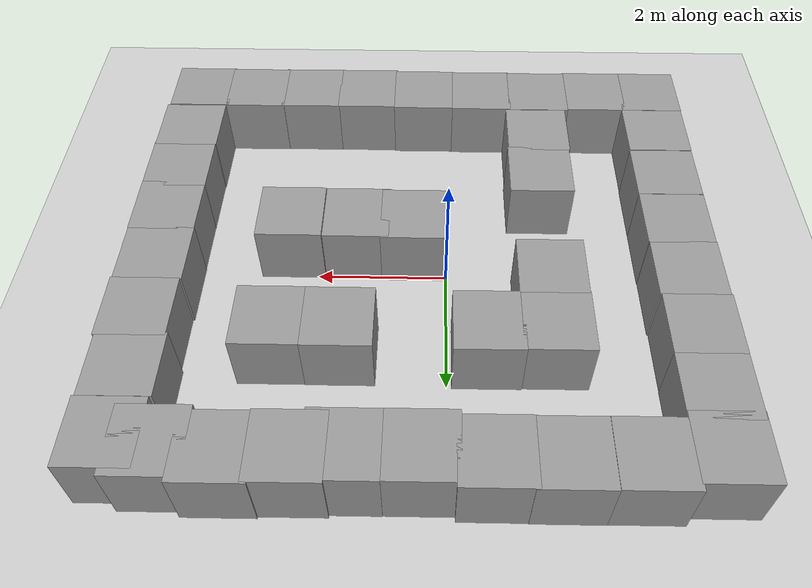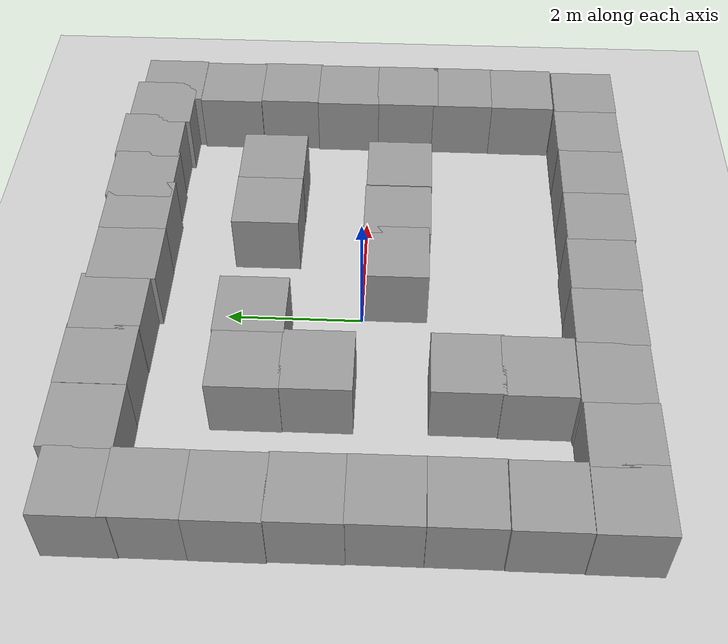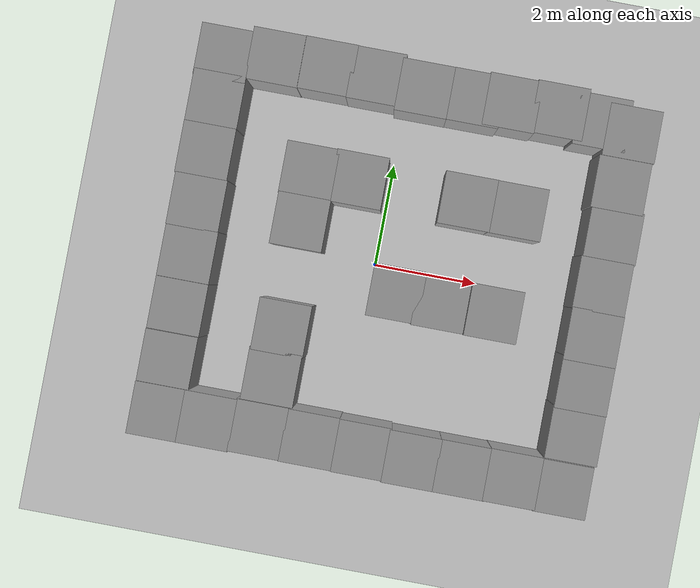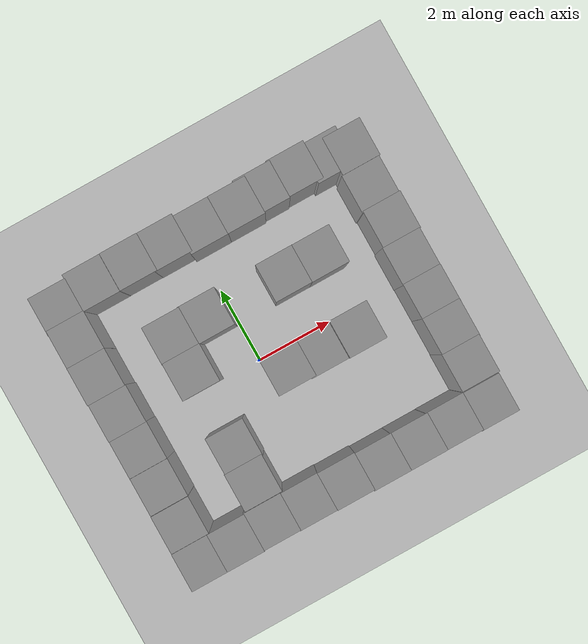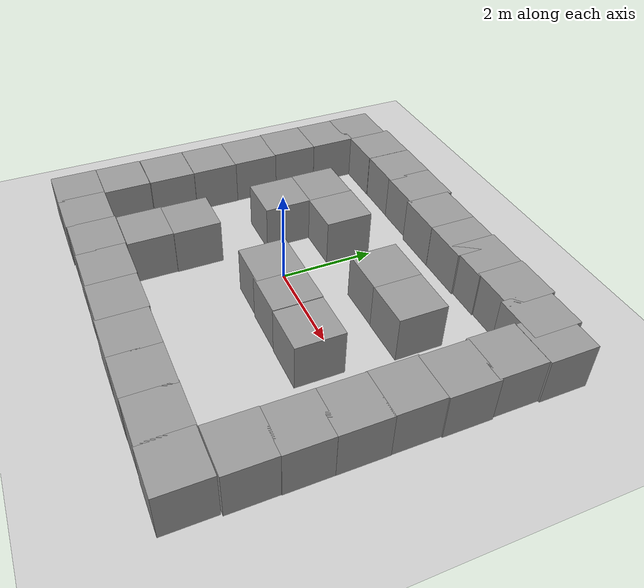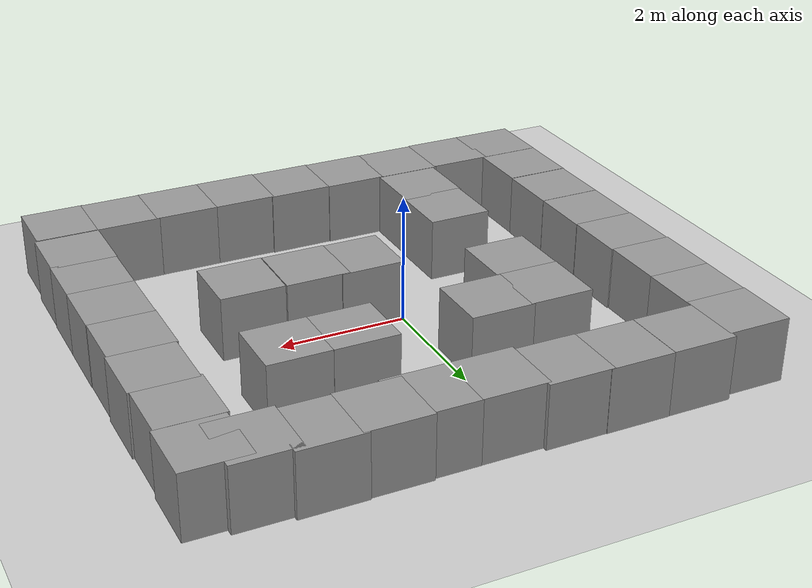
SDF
<sdf version="1.7">
 <world name="default">
  <model name="ground_plane">
   <static>1</static>
   <link name="link">
    <collision name="collision">
     <geometry><plane><normal>0 0 1</normal><size>100 100</size></plane></geometry>
     <surface><friction><ode><mu>100</mu><mu2>50</mu2></ode></friction></surface>
    </collision>
    <visual name="visual">
     <cast_shadows>0</cast_shadows>
     <geometry><plane><normal>0 0 1</normal><size>100 100</size></plane></geometry>
     <material>
      <script><uri>file://media/materials/scripts/gazebo.material</uri><name>Gazebo/Grey</name></script>
     </material>
    </visual>
   </link>
  </model>
  <light name="sun" type="directional">
   <pose>0 0 10 0 -0 0</pose>
   <diffuse>0.8 0.8 0.8 1</diffuse>
   <specular>0.2 0.2 0.2 1</specular>
   <attenuation>
    <range>1000</range>
    <constant>0.9</constant>
    <linear>0.01</linear>
    <quadratic>0.001</quadratic>
   </attenuation>
   <direction>-0.5 0.1 -0.9</direction>
   <spot><inner_angle>0</inner_angle><outer_angle>0</outer_angle><falloff>0</falloff></spot>
  </light>
  <scene><shadows>0</shadows><ambient>0.4 0.4 0.4 1</ambient><background>0.7 0.7 0.7 1</background></scene>
  <physics type="ode">
   <real_time_update_rate>1000</real_time_update_rate>
   <max_step_size>0.001</max_step_size>
   <real_time_factor>1</real_time_factor>
   <ode>
    <solver>
     <type>quick</type>
     <iters>150</iters>
     <precon_iters>0</precon_iters>
     <sor>1.4</sor>
     <use_dynamic_moi_rescaling>1</use_dynamic_moi_rescaling>
    </solver>
    <constraints>
     <cfm>1e-05</cfm>
     <erp>0.2</erp>
     <contact_max_correcting_vel>2000</contact_max_correcting_vel>
     <contact_surface_layer>0.01</contact_surface_layer>
    </constraints>
   </ode>
  </physics>
  <gravity>0 0 -9.8</gravity>
  <magnetic_field>6e-06 2.3e-05 -4.2e-05</magnetic_field>
  <atmosphere type="adiabatic"/>
  <audio><device>default</device></audio>
  <spherical_coordinates>
   <surface_model>EARTH_WGS84</surface_model>
   <latitude_deg>0</latitude_deg>
   <longitude_deg>0</longitude_deg>
   <elevation>0</elevation>
   <heading_deg>0</heading_deg>
  </spherical_coordinates>
  <model name="turtlebot3_world">
   <link name="link_4">
    <inertial>
     <mass>1</mass>
     <inertia>
      <ixx>0.166667</ixx>
      <ixy>0</ixy>
      <ixz>0</ixz>
      <iyy>0.166667</iyy>
      <iyz>0</iyz>
      <izz>0.166667</izz>
     </inertia>
    </inertial>
    <pose>-3.51588 2.52725 0.5 0 -0 0</pose>
    <visual name="visual">
     <geometry><box><size>1 1 1</size></box></geometry>
     <material>
      <lighting>1</lighting>
      <script><uri>file://media/materials/scripts/gazebo.material</uri><name>Gazebo/Grey</name></script>
      <shader type="pixel"/>
     </material>
    </visual>
    <collision name="collision">
     <geometry><box><size>1 1 1</size></box></geometry>
     <surface>
      <friction>
       <ode><mu>1</mu><mu2>1</mu2><fdir1>0 0 0</fdir1><slip1>0</slip1><slip2>0</slip2></ode>
       <torsional>
        <coefficient>1</coefficient>
        <patch_radius>0</patch_radius>
        <surface_radius>0</surface_radius>
        <use_patch_radius>1</use_patch_radius>
        <ode><slip>0</slip></ode>
       </torsional>
      </friction>
      <bounce><restitution_coefficient>0</restitution_coefficient><threshold>1e+06</threshold></bounce>
      <contact>
       <collide_without_contact>0</collide_without_contact>
       <collide_without_contact_bitmask>1</collide_without_contact_bitmask>
       <collide_bitmask>1</collide_bitmask>
       <ode>
        <soft_cfm>0</soft_cfm>
        <soft_erp>0.2</soft_erp>
        <kp>1e+13</kp>
        <kd>1</kd>
        <max_vel>0.01</max_vel>
        <min_depth>0</min_depth>
       </ode>
       <bullet>
        <split_impulse>1</split_impulse>
        <split_impulse_penetration_threshold>-0.01</split_impulse_penetration_threshold>
        <soft_cfm>0</soft_cfm>
        <soft_erp>0.2</soft_erp>
        <kp>1e+13</kp>
        <kd>1</kd>
       </bullet>
      </contact>
     </surface>
    </collision>
   </link>
   <link name="link_4_clone">
    <inertial>
     <mass>1</mass>
     <inertia>
      <ixx>0.166667</ixx>
      <ixy>0</ixy>
      <ixz>0</ixz>
      <iyy>0.166667</iyy>
      <iyz>0</iyz>
      <izz>0.166667</izz>
     </inertia>
    </inertial>
    <pose>-3.51881 1.52869 0.5 0 -0 0</pose>
    <visual name="visual">
     <geometry><box><size>1 1 1</size></box></geometry>
     <material>
      <lighting>1</lighting>
      <script><uri>file://media/materials/scripts/gazebo.material</uri><name>Gazebo/Grey</name></script>
      <shader type="pixel"/>
     </material>
    </visual>
    <collision name="collision">
     <geometry><box><size>1 1 1</size></box></geometry>
     <surface>
      <friction>
       <ode><mu>1</mu><mu2>1</mu2><fdir1>0 0 0</fdir1><slip1>0</slip1><slip2>0</slip2></ode>
       <torsional>
        <coefficient>1</coefficient>
        <patch_radius>0</patch_radius>
        <surface_radius>0</surface_radius>
        <use_patch_radius>1</use_patch_radius>
        <ode><slip>0</slip></ode>
       </torsional>
      </friction>
      <bounce><restitution_coefficient>0</restitution_coefficient><threshold>1e+06</threshold></bounce>
      <contact>
       <collide_without_contact>0</collide_without_contact>
       <collide_without_contact_bitmask>1</collide_without_contact_bitmask>
       <collide_bitmask>1</collide_bitmask>
       <ode>
        <soft_cfm>0</soft_cfm>
        <soft_erp>0.2</soft_erp>
        <kp>1e+13</kp>
        <kd>1</kd>
        <max_vel>0.01</max_vel>
        <min_depth>0</min_depth>
       </ode>
       <bullet>
        <split_impulse>1</split_impulse>
        <split_impulse_penetration_threshold>-0.01</split_impulse_penetration_threshold>
        <soft_cfm>0</soft_cfm>
        <soft_erp>0.2</soft_erp>
        <kp>1e+13</kp>
        <kd>1</kd>
       </bullet>
      </contact>
     </surface>
    </collision>
   </link>
   <link name="link_4_clone_0">
    <inertial>
     <mass>1</mass>
     <inertia>
      <ixx>0.166667</ixx>
      <ixy>0</ixy>
      <ixz>0</ixz>
      <iyy>0.166667</iyy>
      <iyz>0</iyz>
      <izz>0.166667</izz>
     </inertia>
    </inertial>
    <pose>-3.49974 0.540999 0.5 0 -0 0</pose>
    <visual name="visual">
     <geometry><box><size>1 1 1</size></box></geometry>
     <material>
      <lighting>1</lighting>
      <script><uri>file://media/materials/scripts/gazebo.material</uri><name>Gazebo/Grey</name></script>
      <shader type="pixel"/>
     </material>
    </visual>
    <collision name="collision">
     <geometry><box><size>1 1 1</size></box></geometry>
     <surface>
      <friction>
       <ode><mu>1</mu><mu2>1</mu2><fdir1>0 0 0</fdir1><slip1>0</slip1><slip2>0</slip2></ode>
       <torsional>
        <coefficient>1</coefficient>
        <patch_radius>0</patch_radius>
        <surface_radius>0</surface_radius>
        <use_patch_radius>1</use_patch_radius>
        <ode><slip>0</slip></ode>
       </torsional>
      </friction>
      <bounce><restitution_coefficient>0</restitution_coefficient><threshold>1e+06</threshold></bounce>
      <contact>
       <collide_without_contact>0</collide_without_contact>
       <collide_without_contact_bitmask>1</collide_without_contact_bitmask>
       <collide_bitmask>1</collide_bitmask>
       <ode>
        <soft_cfm>0</soft_cfm>
        <soft_erp>0.2</soft_erp>
        <kp>1e+13</kp>
        <kd>1</kd>
        <max_vel>0.01</max_vel>
        <min_depth>0</min_depth>
       </ode>
       <bullet>
        <split_impulse>1</split_impulse>
        <split_impulse_penetration_threshold>-0.01</split_impulse_penetration_threshold>
        <soft_cfm>0</soft_cfm>
        <soft_erp>0.2</soft_erp>
        <kp>1e+13</kp>
        <kd>1</kd>
       </bullet>
      </contact>
     </surface>
    </collision>
   </link>
   <link name="link_4_clone_1">
    <inertial>
     <mass>1</mass>
     <inertia>
      <ixx>0.166667</ixx>
      <ixy>0</ixy>
      <ixz>0</ixz>
      <iyy>0.166667</iyy>
      <iyz>0</iyz>
      <izz>0.166667</izz>
     </inertia>
    </inertial>
    <pose>-3.49177 -0.443894 0.5 0 -0 0</pose>
    <visual name="visual">
     <geometry><box><size>1 1 1</size></box></geometry>
     <material>
      <lighting>1</lighting>
      <script><uri>file://media/materials/scripts/gazebo.material</uri><name>Gazebo/Grey</name></script>
      <shader type="pixel"/>
     </material>
    </visual>
    <collision name="collision">
     <geometry><box><size>1 1 1</size></box></geometry>
     <surface>
      <friction>
       <ode><mu>1</mu><mu2>1</mu2><fdir1>0 0 0</fdir1><slip1>0</slip1><slip2>0</slip2></ode>
       <torsional>
        <coefficient>1</coefficient>
        <patch_radius>0</patch_radius>
        <surface_radius>0</surface_radius>
        <use_patch_radius>1</use_patch_radius>
        <ode><slip>0</slip></ode>
       </torsional>
      </friction>
      <bounce><restitution_coefficient>0</restitution_coefficient><threshold>1e+06</threshold></bounce>
      <contact>
       <collide_without_contact>0</collide_without_contact>
       <collide_without_contact_bitmask>1</collide_without_contact_bitmask>
       <collide_bitmask>1</collide_bitmask>
       <ode>
        <soft_cfm>0</soft_cfm>
        <soft_erp>0.2</soft_erp>
        <kp>1e+13</kp>
        <kd>1</kd>
        <max_vel>0.01</max_vel>
        <min_depth>0</min_depth>
       </ode>
       <bullet>
        <split_impulse>1</split_impulse>
        <split_impulse_penetration_threshold>-0.01</split_impulse_penetration_threshold>
        <soft_cfm>0</soft_cfm>
        <soft_erp>0.2</soft_erp>
        <kp>1e+13</kp>
        <kd>1</kd>
       </bullet>
      </contact>
     </surface>
    </collision>
   </link>
   <link name="link_4_clone_10">
    <inertial>
     <mass>1</mass>
     <inertia>
      <ixx>0.166667</ixx>
      <ixy>0</ixy>
      <ixz>0</ixz>
      <iyy>0.166667</iyy>
      <iyz>0</iyz>
      <izz>0.166667</izz>
     </inertia>
    </inertial>
    <pose>1.31695 3.4392 0.5 0 -0 0</pose>
    <visual name="visual">
     <geometry><box><size>1 1 1</size></box></geometry>
     <material>
      <lighting>1</lighting>
      <script><uri>file://media/materials/scripts/gazebo.material</uri><name>Gazebo/Grey</name></script>
      <shader type="pixel"/>
     </material>
    </visual>
    <collision name="collision">
     <geometry><box><size>1 1 1</size></box></geometry>
     <surface>
      <friction>
       <ode><mu>1</mu><mu2>1</mu2><fdir1>0 0 0</fdir1><slip1>0</slip1><slip2>0</slip2></ode>
       <torsional>
        <coefficient>1</coefficient>
        <patch_radius>0</patch_radius>
        <surface_radius>0</surface_radius>
        <use_patch_radius>1</use_patch_radius>
        <ode><slip>0</slip></ode>
       </torsional>
      </friction>
      <bounce><restitution_coefficient>0</restitution_coefficient><threshold>1e+06</threshold></bounce>
      <contact>
       <collide_without_contact>0</collide_without_contact>
       <collide_without_contact_bitmask>1</collide_without_contact_bitmask>
       <collide_bitmask>1</collide_bitmask>
       <ode>
        <soft_cfm>0</soft_cfm>
        <soft_erp>0.2</soft_erp>
        <kp>1e+13</kp>
        <kd>1</kd>
        <max_vel>0.01</max_vel>
        <min_depth>0</min_depth>
       </ode>
       <bullet>
        <split_impulse>1</split_impulse>
        <split_impulse_penetration_threshold>-0.01</split_impulse_penetration_threshold>
        <soft_cfm>0</soft_cfm>
        <soft_erp>0.2</soft_erp>
        <kp>1e+13</kp>
        <kd>1</kd>
       </bullet>
      </contact>
     </surface>
    </collision>
   </link>
   <link name="link_4_clone_11">
    <inertial>
     <mass>1</mass>
     <inertia>
      <ixx>0.166667</ixx>
      <ixy>0</ixy>
      <ixz>0</ixz>
      <iyy>0.166667</iyy>
      <iyz>0</iyz>
      <izz>0.166667</izz>
     </inertia>
    </inertial>
    <pose>2.00157 3.47266 0.5 0 -0 0</pose>
    <visual name="visual">
     <geometry><box><size>1 1 1</size></box></geometry>
     <material>
      <lighting>1</lighting>
      <script><uri>file://media/materials/scripts/gazebo.material</uri><name>Gazebo/Grey</name></script>
      <shader type="pixel"/>
     </material>
    </visual>
    <collision name="collision">
     <geometry><box><size>1 1 1</size></box></geometry>
     <surface>
      <friction>
       <ode><mu>1</mu><mu2>1</mu2><fdir1>0 0 0</fdir1><slip1>0</slip1><slip2>0</slip2></ode>
       <torsional>
        <coefficient>1</coefficient>
        <patch_radius>0</patch_radius>
        <surface_radius>0</surface_radius>
        <use_patch_radius>1</use_patch_radius>
        <ode><slip>0</slip></ode>
       </torsional>
      </friction>
      <bounce><restitution_coefficient>0</restitution_coefficient><threshold>1e+06</threshold></bounce>
      <contact>
       <collide_without_contact>0</collide_without_contact>
       <collide_without_contact_bitmask>1</collide_without_contact_bitmask>
       <collide_bitmask>1</collide_bitmask>
       <ode>
        <soft_cfm>0</soft_cfm>
        <soft_erp>0.2</soft_erp>
        <kp>1e+13</kp>
        <kd>1</kd>
        <max_vel>0.01</max_vel>
        <min_depth>0</min_depth>
       </ode>
       <bullet>
        <split_impulse>1</split_impulse>
        <split_impulse_penetration_threshold>-0.01</split_impulse_penetration_threshold>
        <soft_cfm>0</soft_cfm>
        <soft_erp>0.2</soft_erp>
        <kp>1e+13</kp>
        <kd>1</kd>
       </bullet>
      </contact>
     </surface>
    </collision>
   </link>
   <link name="link_4_clone_12">
    <inertial>
     <mass>1</mass>
     <inertia>
      <ixx>0.166667</ixx>
      <ixy>0</ixy>
      <ixz>0</ixz>
      <iyy>0.166667</iyy>
      <iyz>0</iyz>
      <izz>0.166667</izz>
     </inertia>
    </inertial>
    <pose>2.91323 3.4956 0.5 0 -0 0</pose>
    <visual name="visual">
     <geometry><box><size>1 1 1</size></box></geometry>
     <material>
      <lighting>1</lighting>
      <script><uri>file://media/materials/scripts/gazebo.material</uri><name>Gazebo/Grey</name></script>
      <shader type="pixel"/>
     </material>
    </visual>
    <collision name="collision">
     <geometry><box><size>1 1 1</size></box></geometry>
     <surface>
      <friction>
       <ode><mu>1</mu><mu2>1</mu2><fdir1>0 0 0</fdir1><slip1>0</slip1><slip2>0</slip2></ode>
       <torsional>
        <coefficient>1</coefficient>
        <patch_radius>0</patch_radius>
        <surface_radius>0</surface_radius>
        <use_patch_radius>1</use_patch_radius>
        <ode><slip>0</slip></ode>
       </torsional>
      </friction>
      <bounce><restitution_coefficient>0</restitution_coefficient><threshold>1e+06</threshold></bounce>
      <contact>
       <collide_without_contact>0</collide_without_contact>
       <collide_without_contact_bitmask>1</collide_without_contact_bitmask>
       <collide_bitmask>1</collide_bitmask>
       <ode>
        <soft_cfm>0</soft_cfm>
        <soft_erp>0.2</soft_erp>
        <kp>1e+13</kp>
        <kd>1</kd>
        <max_vel>0.01</max_vel>
        <min_depth>0</min_depth>
       </ode>
       <bullet>
        <split_impulse>1</split_impulse>
        <split_impulse_penetration_threshold>-0.01</split_impulse_penetration_threshold>
        <soft_cfm>0</soft_cfm>
        <soft_erp>0.2</soft_erp>
        <kp>1e+13</kp>
        <kd>1</kd>
       </bullet>
      </contact>
     </surface>
    </collision>
   </link>
   <link name="link_4_clone_13">
    <inertial>
     <mass>1</mass>
     <inertia>
      <ixx>0.166667</ixx>
      <ixy>0</ixy>
      <ixz>0</ixz>
      <iyy>0.166667</iyy>
      <iyz>0</iyz>
      <izz>0.166667</izz>
     </inertia>
    </inertial>
    <pose>-2.56143 -3.46208 0.5 0 -0 0</pose>
    <visual name="visual">
     <geometry><box><size>1 1 1</size></box></geometry>
     <material>
      <lighting>1</lighting>
      <script><uri>file://media/materials/scripts/gazebo.material</uri><name>Gazebo/Grey</name></script>
      <shader type="pixel"/>
     </material>
    </visual>
    <collision name="collision">
     <geometry><box><size>1 1 1</size></box></geometry>
     <surface>
      <friction>
       <ode><mu>1</mu><mu2>1</mu2><fdir1>0 0 0</fdir1><slip1>0</slip1><slip2>0</slip2></ode>
       <torsional>
        <coefficient>1</coefficient>
        <patch_radius>0</patch_radius>
        <surface_radius>0</surface_radius>
        <use_patch_radius>1</use_patch_radius>
        <ode><slip>0</slip></ode>
       </torsional>
      </friction>
      <bounce><restitution_coefficient>0</restitution_coefficient><threshold>1e+06</threshold></bounce>
      <contact>
       <collide_without_contact>0</collide_without_contact>
       <collide_without_contact_bitmask>1</collide_without_contact_bitmask>
       <collide_bitmask>1</collide_bitmask>
       <ode>
        <soft_cfm>0</soft_cfm>
        <soft_erp>0.2</soft_erp>
        <kp>1e+13</kp>
        <kd>1</kd>
        <max_vel>0.01</max_vel>
        <min_depth>0</min_depth>
       </ode>
       <bullet>
        <split_impulse>1</split_impulse>
        <split_impulse_penetration_threshold>-0.01</split_impulse_penetration_threshold>
        <soft_cfm>0</soft_cfm>
        <soft_erp>0.2</soft_erp>
        <kp>1e+13</kp>
        <kd>1</kd>
       </bullet>
      </contact>
     </surface>
    </collision>
   </link>
   <link name="link_4_clone_14">
    <inertial>
     <mass>1</mass>
     <inertia>
      <ixx>0.166667</ixx>
      <ixy>0</ixy>
      <ixz>0</ixz>
      <iyy>0.166667</iyy>
      <iyz>0</iyz>
      <izz>0.166667</izz>
     </inertia>
    </inertial>
    <pose>-1.57857 -3.44426 0.5 0 -0 0</pose>
    <visual name="visual">
     <geometry><box><size>1 1 1</size></box></geometry>
     <material>
      <lighting>1</lighting>
      <script><uri>file://media/materials/scripts/gazebo.material</uri><name>Gazebo/Grey</name></script>
      <shader type="pixel"/>
     </material>
    </visual>
    <collision name="collision">
     <geometry><box><size>1 1 1</size></box></geometry>
     <surface>
      <friction>
       <ode><mu>1</mu><mu2>1</mu2><fdir1>0 0 0</fdir1><slip1>0</slip1><slip2>0</slip2></ode>
       <torsional>
        <coefficient>1</coefficient>
        <patch_radius>0</patch_radius>
        <surface_radius>0</surface_radius>
        <use_patch_radius>1</use_patch_radius>
        <ode><slip>0</slip></ode>
       </torsional>
      </friction>
      <bounce><restitution_coefficient>0</restitution_coefficient><threshold>1e+06</threshold></bounce>
      <contact>
       <collide_without_contact>0</collide_without_contact>
       <collide_without_contact_bitmask>1</collide_without_contact_bitmask>
       <collide_bitmask>1</collide_bitmask>
       <ode>
        <soft_cfm>0</soft_cfm>
        <soft_erp>0.2</soft_erp>
        <kp>1e+13</kp>
        <kd>1</kd>
        <max_vel>0.01</max_vel>
        <min_depth>0</min_depth>
       </ode>
       <bullet>
        <split_impulse>1</split_impulse>
        <split_impulse_penetration_threshold>-0.01</split_impulse_penetration_threshold>
        <soft_cfm>0</soft_cfm>
        <soft_erp>0.2</soft_erp>
        <kp>1e+13</kp>
        <kd>1</kd>
       </bullet>
      </contact>
     </surface>
    </collision>
   </link>
   <link name="link_4_clone_15">
    <inertial>
     <mass>1</mass>
     <inertia>
      <ixx>0.166667</ixx>
      <ixy>0</ixy>
      <ixz>0</ixz>
      <iyy>0.166667</iyy>
      <iyz>0</iyz>
      <izz>0.166667</izz>
     </inertia>
    </inertial>
    <pose>-0.599535 -3.45421 0.5 0 -0 0</pose>
    <visual name="visual">
     <geometry><box><size>1 1 1</size></box></geometry>
     <material>
      <lighting>1</lighting>
      <script><uri>file://media/materials/scripts/gazebo.material</uri><name>Gazebo/Grey</name></script>
      <shader type="pixel"/>
     </material>
    </visual>
    <collision name="collision">
     <geometry><box><size>1 1 1</size></box></geometry>
     <surface>
      <friction>
       <ode><mu>1</mu><mu2>1</mu2><fdir1>0 0 0</fdir1><slip1>0</slip1><slip2>0</slip2></ode>
       <torsional>
        <coefficient>1</coefficient>
        <patch_radius>0</patch_radius>
        <surface_radius>0</surface_radius>
        <use_patch_radius>1</use_patch_radius>
        <ode><slip>0</slip></ode>
       </torsional>
      </friction>
      <bounce><restitution_coefficient>0</restitution_coefficient><threshold>1e+06</threshold></bounce>
      <contact>
       <collide_without_contact>0</collide_without_contact>
       <collide_without_contact_bitmask>1</collide_without_contact_bitmask>
       <collide_bitmask>1</collide_bitmask>
       <ode>
        <soft_cfm>0</soft_cfm>
        <soft_erp>0.2</soft_erp>
        <kp>1e+13</kp>
        <kd>1</kd>
        <max_vel>0.01</max_vel>
        <min_depth>0</min_depth>
       </ode>
       <bullet>
        <split_impulse>1</split_impulse>
        <split_impulse_penetration_threshold>-0.01</split_impulse_penetration_threshold>
        <soft_cfm>0</soft_cfm>
        <soft_erp>0.2</soft_erp>
        <kp>1e+13</kp>
        <kd>1</kd>
       </bullet>
      </contact>
     </surface>
    </collision>
   </link>
   <link name="link_4_clone_16">
    <inertial>
     <mass>1</mass>
     <inertia>
      <ixx>0.166667</ixx>
      <ixy>0</ixy>
      <ixz>0</ixz>
      <iyy>0.166667</iyy>
      <iyz>0</iyz>
      <izz>0.166667</izz>
     </inertia>
    </inertial>
    <pose>0.398656 -3.46623 0.5 0 -0 0</pose>
    <visual name="visual">
     <geometry><box><size>1 1 1</size></box></geometry>
     <material>
      <lighting>1</lighting>
      <script><uri>file://media/materials/scripts/gazebo.material</uri><name>Gazebo/Grey</name></script>
      <shader type="pixel"/>
     </material>
    </visual>
    <collision name="collision">
     <geometry><box><size>1 1 1</size></box></geometry>
     <surface>
      <friction>
       <ode><mu>1</mu><mu2>1</mu2><fdir1>0 0 0</fdir1><slip1>0</slip1><slip2>0</slip2></ode>
       <torsional>
        <coefficient>1</coefficient>
        <patch_radius>0</patch_radius>
        <surface_radius>0</surface_radius>
        <use_patch_radius>1</use_patch_radius>
        <ode><slip>0</slip></ode>
       </torsional>
      </friction>
      <bounce><restitution_coefficient>0</restitution_coefficient><threshold>1e+06</threshold></bounce>
      <contact>
       <collide_without_contact>0</collide_without_contact>
       <collide_without_contact_bitmask>1</collide_without_contact_bitmask>
       <collide_bitmask>1</collide_bitmask>
       <ode>
        <soft_cfm>0</soft_cfm>
        <soft_erp>0.2</soft_erp>
        <kp>1e+13</kp>
        <kd>1</kd>
        <max_vel>0.01</max_vel>
        <min_depth>0</min_depth>
       </ode>
       <bullet>
        <split_impulse>1</split_impulse>
        <split_impulse_penetration_threshold>-0.01</split_impulse_penetration_threshold>
        <soft_cfm>0</soft_cfm>
        <soft_erp>0.2</soft_erp>
        <kp>1e+13</kp>
        <kd>1</kd>
       </bullet>
      </contact>
     </surface>
    </collision>
   </link>
   <link name="link_4_clone_17">
    <inertial>
     <mass>1</mass>
     <inertia>
      <ixx>0.166667</ixx>
      <ixy>0</ixy>
      <ixz>0</ixz>
      <iyy>0.166667</iyy>
      <iyz>0</iyz>
      <izz>0.166667</izz>
     </inertia>
    </inertial>
    <pose>1.36667 -3.48701 0.5 0 -0 0</pose>
    <visual name="visual">
     <geometry><box><size>1 1 1</size></box></geometry>
     <material>
      <lighting>1</lighting>
      <script><uri>file://media/materials/scripts/gazebo.material</uri><name>Gazebo/Grey</name></script>
      <shader type="pixel"/>
     </material>
    </visual>
    <collision name="collision">
     <geometry><box><size>1 1 1</size></box></geometry>
     <surface>
      <friction>
       <ode><mu>1</mu><mu2>1</mu2><fdir1>0 0 0</fdir1><slip1>0</slip1><slip2>0</slip2></ode>
       <torsional>
        <coefficient>1</coefficient>
        <patch_radius>0</patch_radius>
        <surface_radius>0</surface_radius>
        <use_patch_radius>1</use_patch_radius>
        <ode><slip>0</slip></ode>
       </torsional>
      </friction>
      <bounce><restitution_coefficient>0</restitution_coefficient><threshold>1e+06</threshold></bounce>
      <contact>
       <collide_without_contact>0</collide_without_contact>
       <collide_without_contact_bitmask>1</collide_without_contact_bitmask>
       <collide_bitmask>1</collide_bitmask>
       <ode>
        <soft_cfm>0</soft_cfm>
        <soft_erp>0.2</soft_erp>
        <kp>1e+13</kp>
        <kd>1</kd>
        <max_vel>0.01</max_vel>
        <min_depth>0</min_depth>
       </ode>
       <bullet>
        <split_impulse>1</split_impulse>
        <split_impulse_penetration_threshold>-0.01</split_impulse_penetration_threshold>
        <soft_cfm>0</soft_cfm>
        <soft_erp>0.2</soft_erp>
        <kp>1e+13</kp>
        <kd>1</kd>
       </bullet>
      </contact>
     </surface>
    </collision>
   </link>
   <link name="link_4_clone_18">
    <inertial>
     <mass>1</mass>
     <inertia>
      <ixx>0.166667</ixx>
      <ixy>0</ixy>
      <ixz>0</ixz>
      <iyy>0.166667</iyy>
      <iyz>0</iyz>
      <izz>0.166667</izz>
     </inertia>
    </inertial>
    <pose>2.34696 -3.48647 0.5 0 -0 0</pose>
    <visual name="visual">
     <geometry><box><size>1 1 1</size></box></geometry>
     <material>
      <lighting>1</lighting>
      <script><uri>file://media/materials/scripts/gazebo.material</uri><name>Gazebo/Grey</name></script>
      <shader type="pixel"/>
     </material>
    </visual>
    <collision name="collision">
     <geometry><box><size>1 1 1</size></box></geometry>
     <surface>
      <friction>
       <ode><mu>1</mu><mu2>1</mu2><fdir1>0 0 0</fdir1><slip1>0</slip1><slip2>0</slip2></ode>
       <torsional>
        <coefficient>1</coefficient>
        <patch_radius>0</patch_radius>
        <surface_radius>0</surface_radius>
        <use_patch_radius>1</use_patch_radius>
        <ode><slip>0</slip></ode>
       </torsional>
      </friction>
      <bounce><restitution_coefficient>0</restitution_coefficient><threshold>1e+06</threshold></bounce>
      <contact>
       <collide_without_contact>0</collide_without_contact>
       <collide_without_contact_bitmask>1</collide_without_contact_bitmask>
       <collide_bitmask>1</collide_bitmask>
       <ode>
        <soft_cfm>0</soft_cfm>
        <soft_erp>0.2</soft_erp>
        <kp>1e+13</kp>
        <kd>1</kd>
        <max_vel>0.01</max_vel>
        <min_depth>0</min_depth>
       </ode>
       <bullet>
        <split_impulse>1</split_impulse>
        <split_impulse_penetration_threshold>-0.01</split_impulse_penetration_threshold>
        <soft_cfm>0</soft_cfm>
        <soft_erp>0.2</soft_erp>
        <kp>1e+13</kp>
        <kd>1</kd>
       </bullet>
      </contact>
     </surface>
    </collision>
   </link>
   <link name="link_4_clone_19">
    <inertial>
     <mass>1</mass>
     <inertia>
      <ixx>0.166667</ixx>
      <ixy>0</ixy>
      <ixz>0</ixz>
      <iyy>0.166667</iyy>
      <iyz>0</iyz>
      <izz>0.166667</izz>
     </inertia>
    </inertial>
    <pose>3.30228 -3.48091 0.5 0 -0 0</pose>
    <visual name="visual">
     <geometry><box><size>1 1 1</size></box></geometry>
     <material>
      <lighting>1</lighting>
      <script><uri>file://media/materials/scripts/gazebo.material</uri><name>Gazebo/Grey</name></script>
      <shader type="pixel"/>
     </material>
    </visual>
    <collision name="collision">
     <geometry><box><size>1 1 1</size></box></geometry>
     <surface>
      <friction>
       <ode><mu>1</mu><mu2>1</mu2><fdir1>0 0 0</fdir1><slip1>0</slip1><slip2>0</slip2></ode>
       <torsional>
        <coefficient>1</coefficient>
        <patch_radius>0</patch_radius>
        <surface_radius>0</surface_radius>
        <use_patch_radius>1</use_patch_radius>
        <ode><slip>0</slip></ode>
       </torsional>
      </friction>
      <bounce><restitution_coefficient>0</restitution_coefficient><threshold>1e+06</threshold></bounce>
      <contact>
       <collide_without_contact>0</collide_without_contact>
       <collide_without_contact_bitmask>1</collide_without_contact_bitmask>
       <collide_bitmask>1</collide_bitmask>
       <ode>
        <soft_cfm>0</soft_cfm>
        <soft_erp>0.2</soft_erp>
        <kp>1e+13</kp>
        <kd>1</kd>
        <max_vel>0.01</max_vel>
        <min_depth>0</min_depth>
       </ode>
       <bullet>
        <split_impulse>1</split_impulse>
        <split_impulse_penetration_threshold>-0.01</split_impulse_penetration_threshold>
        <soft_cfm>0</soft_cfm>
        <soft_erp>0.2</soft_erp>
        <kp>1e+13</kp>
        <kd>1</kd>
       </bullet>
      </contact>
     </surface>
    </collision>
   </link>
   <link name="link_4_clone_2">
    <inertial>
     <mass>1</mass>
     <inertia>
      <ixx>0.166667</ixx>
      <ixy>0</ixy>
      <ixz>0</ixz>
      <iyy>0.166667</iyy>
      <iyz>0</iyz>
      <izz>0.166667</izz>
     </inertia>
    </inertial>
    <pose>-3.49078 -1.44711 0.5 0 -0 0</pose>
    <visual name="visual">
     <geometry><box><size>1 1 1</size></box></geometry>
     <material>
      <lighting>1</lighting>
      <script><uri>file://media/materials/scripts/gazebo.material</uri><name>Gazebo/Grey</name></script>
      <shader type="pixel"/>
     </material>
    </visual>
    <collision name="collision">
     <geometry><box><size>1 1 1</size></box></geometry>
     <surface>
      <friction>
       <ode><mu>1</mu><mu2>1</mu2><fdir1>0 0 0</fdir1><slip1>0</slip1><slip2>0</slip2></ode>
       <torsional>
        <coefficient>1</coefficient>
        <patch_radius>0</patch_radius>
        <surface_radius>0</surface_radius>
        <use_patch_radius>1</use_patch_radius>
        <ode><slip>0</slip></ode>
       </torsional>
      </friction>
      <bounce><restitution_coefficient>0</restitution_coefficient><threshold>1e+06</threshold></bounce>
      <contact>
       <collide_without_contact>0</collide_without_contact>
       <collide_without_contact_bitmask>1</collide_without_contact_bitmask>
       <collide_bitmask>1</collide_bitmask>
       <ode>
        <soft_cfm>0</soft_cfm>
        <soft_erp>0.2</soft_erp>
        <kp>1e+13</kp>
        <kd>1</kd>
        <max_vel>0.01</max_vel>
        <min_depth>0</min_depth>
       </ode>
       <bullet>
        <split_impulse>1</split_impulse>
        <split_impulse_penetration_threshold>-0.01</split_impulse_penetration_threshold>
        <soft_cfm>0</soft_cfm>
        <soft_erp>0.2</soft_erp>
        <kp>1e+13</kp>
        <kd>1</kd>
       </bullet>
      </contact>
     </surface>
    </collision>
   </link>
   <link name="link_4_clone_20">
    <inertial>
     <mass>1</mass>
     <inertia>
      <ixx>0.166667</ixx>
      <ixy>0</ixy>
      <ixz>0</ixz>
      <iyy>0.166667</iyy>
      <iyz>0</iyz>
      <izz>0.166667</izz>
     </inertia>
    </inertial>
    <pose>4.26068 -3.49093 0.5 0 -0 0</pose>
    <visual name="visual">
     <geometry><box><size>1 1 1</size></box></geometry>
     <material>
      <lighting>1</lighting>
      <script><uri>file://media/materials/scripts/gazebo.material</uri><name>Gazebo/Grey</name></script>
      <shader type="pixel"/>
     </material>
    </visual>
    <collision name="collision">
     <geometry><box><size>1 1 1</size></box></geometry>
     <surface>
      <friction>
       <ode><mu>1</mu><mu2>1</mu2><fdir1>0 0 0</fdir1><slip1>0</slip1><slip2>0</slip2></ode>
       <torsional>
        <coefficient>1</coefficient>
        <patch_radius>0</patch_radius>
        <surface_radius>0</surface_radius>
        <use_patch_radius>1</use_patch_radius>
        <ode><slip>0</slip></ode>
       </torsional>
      </friction>
      <bounce><restitution_coefficient>0</restitution_coefficient><threshold>1e+06</threshold></bounce>
      <contact>
       <collide_without_contact>0</collide_without_contact>
       <collide_without_contact_bitmask>1</collide_without_contact_bitmask>
       <collide_bitmask>1</collide_bitmask>
       <ode>
        <soft_cfm>0</soft_cfm>
        <soft_erp>0.2</soft_erp>
        <kp>1e+13</kp>
        <kd>1</kd>
        <max_vel>0.01</max_vel>
        <min_depth>0</min_depth>
       </ode>
       <bullet>
        <split_impulse>1</split_impulse>
        <split_impulse_penetration_threshold>-0.01</split_impulse_penetration_threshold>
        <soft_cfm>0</soft_cfm>
        <soft_erp>0.2</soft_erp>
        <kp>1e+13</kp>
        <kd>1</kd>
       </bullet>
      </contact>
     </surface>
    </collision>
   </link>
   <link name="link_4_clone_21">
    <inertial>
     <mass>1</mass>
     <inertia>
      <ixx>0.166667</ixx>
      <ixy>0</ixy>
      <ixz>0</ixz>
      <iyy>0.166667</iyy>
      <iyz>0</iyz>
      <izz>0.166667</izz>
     </inertia>
    </inertial>
    <pose>4.29918 -2.47182 0.5 0 -0 0</pose>
    <visual name="visual">
     <geometry><box><size>1 1 1</size></box></geometry>
     <material>
      <lighting>1</lighting>
      <script><uri>file://media/materials/scripts/gazebo.material</uri><name>Gazebo/Grey</name></script>
      <shader type="pixel"/>
     </material>
    </visual>
    <collision name="collision">
     <geometry><box><size>1 1 1</size></box></geometry>
     <surface>
      <friction>
       <ode><mu>1</mu><mu2>1</mu2><fdir1>0 0 0</fdir1><slip1>0</slip1><slip2>0</slip2></ode>
       <torsional>
        <coefficient>1</coefficient>
        <patch_radius>0</patch_radius>
        <surface_radius>0</surface_radius>
        <use_patch_radius>1</use_patch_radius>
        <ode><slip>0</slip></ode>
       </torsional>
      </friction>
      <bounce><restitution_coefficient>0</restitution_coefficient><threshold>1e+06</threshold></bounce>
      <contact>
       <collide_without_contact>0</collide_without_contact>
       <collide_without_contact_bitmask>1</collide_without_contact_bitmask>
       <collide_bitmask>1</collide_bitmask>
       <ode>
        <soft_cfm>0</soft_cfm>
        <soft_erp>0.2</soft_erp>
        <kp>1e+13</kp>
        <kd>1</kd>
        <max_vel>0.01</max_vel>
        <min_depth>0</min_depth>
       </ode>
       <bullet>
        <split_impulse>1</split_impulse>
        <split_impulse_penetration_threshold>-0.01</split_impulse_penetration_threshold>
        <soft_cfm>0</soft_cfm>
        <soft_erp>0.2</soft_erp>
        <kp>1e+13</kp>
        <kd>1</kd>
       </bullet>
      </contact>
     </surface>
    </collision>
   </link>
   <link name="link_4_clone_22">
    <inertial>
     <mass>1</mass>
     <inertia>
      <ixx>0.166667</ixx>
      <ixy>0</ixy>
      <ixz>0</ixz>
      <iyy>0.166667</iyy>
      <iyz>0</iyz>
      <izz>0.166667</izz>
     </inertia>
    </inertial>
    <pose>4.3084 -1.51402 0.5 0 -0 0</pose>
    <visual name="visual">
     <geometry><box><size>1 1 1</size></box></geometry>
     <material>
      <lighting>1</lighting>
      <script><uri>file://media/materials/scripts/gazebo.material</uri><name>Gazebo/Grey</name></script>
      <shader type="pixel"/>
     </material>
    </visual>
    <collision name="collision">
     <geometry><box><size>1 1 1</size></box></geometry>
     <surface>
      <friction>
       <ode><mu>1</mu><mu2>1</mu2><fdir1>0 0 0</fdir1><slip1>0</slip1><slip2>0</slip2></ode>
       <torsional>
        <coefficient>1</coefficient>
        <patch_radius>0</patch_radius>
        <surface_radius>0</surface_radius>
        <use_patch_radius>1</use_patch_radius>
        <ode><slip>0</slip></ode>
       </torsional>
      </friction>
      <bounce><restitution_coefficient>0</restitution_coefficient><threshold>1e+06</threshold></bounce>
      <contact>
       <collide_without_contact>0</collide_without_contact>
       <collide_without_contact_bitmask>1</collide_without_contact_bitmask>
       <collide_bitmask>1</collide_bitmask>
       <ode>
        <soft_cfm>0</soft_cfm>
        <soft_erp>0.2</soft_erp>
        <kp>1e+13</kp>
        <kd>1</kd>
        <max_vel>0.01</max_vel>
        <min_depth>0</min_depth>
       </ode>
       <bullet>
        <split_impulse>1</split_impulse>
        <split_impulse_penetration_threshold>-0.01</split_impulse_penetration_threshold>
        <soft_cfm>0</soft_cfm>
        <soft_erp>0.2</soft_erp>
        <kp>1e+13</kp>
        <kd>1</kd>
       </bullet>
      </contact>
     </surface>
    </collision>
   </link>
   <link name="link_4_clone_23">
    <inertial>
     <mass>1</mass>
     <inertia>
      <ixx>0.166667</ixx>
      <ixy>0</ixy>
      <ixz>0</ixz>
      <iyy>0.166667</iyy>
      <iyz>0</iyz>
      <izz>0.166667</izz>
     </inertia>
    </inertial>
    <pose>4.31032 -0.590382 0.5 0 -0 0</pose>
    <visual name="visual">
     <geometry><box><size>1 1 1</size></box></geometry>
     <material>
      <lighting>1</lighting>
      <script><uri>file://media/materials/scripts/gazebo.material</uri><name>Gazebo/Grey</name></script>
      <shader type="pixel"/>
     </material>
    </visual>
    <collision name="collision">
     <geometry><box><size>1 1 1</size></box></geometry>
     <surface>
      <friction>
       <ode><mu>1</mu><mu2>1</mu2><fdir1>0 0 0</fdir1><slip1>0</slip1><slip2>0</slip2></ode>
       <torsional>
        <coefficient>1</coefficient>
        <patch_radius>0</patch_radius>
        <surface_radius>0</surface_radius>
        <use_patch_radius>1</use_patch_radius>
        <ode><slip>0</slip></ode>
       </torsional>
      </friction>
      <bounce><restitution_coefficient>0</restitution_coefficient><threshold>1e+06</threshold></bounce>
      <contact>
       <collide_without_contact>0</collide_without_contact>
       <collide_without_contact_bitmask>1</collide_without_contact_bitmask>
       <collide_bitmask>1</collide_bitmask>
       <ode>
        <soft_cfm>0</soft_cfm>
        <soft_erp>0.2</soft_erp>
        <kp>1e+13</kp>
        <kd>1</kd>
        <max_vel>0.01</max_vel>
        <min_depth>0</min_depth>
       </ode>
       <bullet>
        <split_impulse>1</split_impulse>
        <split_impulse_penetration_threshold>-0.01</split_impulse_penetration_threshold>
        <soft_cfm>0</soft_cfm>
        <soft_erp>0.2</soft_erp>
        <kp>1e+13</kp>
        <kd>1</kd>
       </bullet>
      </contact>
     </surface>
    </collision>
   </link>
   <link name="link_4_clone_24">
    <inertial>
     <mass>1</mass>
     <inertia>
      <ixx>0.166667</ixx>
      <ixy>0</ixy>
      <ixz>0</ixz>
      <iyy>0.166667</iyy>
      <iyz>0</iyz>
      <izz>0.166667</izz>
     </inertia>
    </inertial>
    <pose>4.30342 0.387083 0.5 0 -0 0</pose>
    <visual name="visual">
     <geometry><box><size>1 1 1</size></box></geometry>
     <material>
      <lighting>1</lighting>
      <script><uri>file://media/materials/scripts/gazebo.material</uri><name>Gazebo/Grey</name></script>
      <shader type="pixel"/>
     </material>
    </visual>
    <collision name="collision">
     <geometry><box><size>1 1 1</size></box></geometry>
     <surface>
      <friction>
       <ode><mu>1</mu><mu2>1</mu2><fdir1>0 0 0</fdir1><slip1>0</slip1><slip2>0</slip2></ode>
       <torsional>
        <coefficient>1</coefficient>
        <patch_radius>0</patch_radius>
        <surface_radius>0</surface_radius>
        <use_patch_radius>1</use_patch_radius>
        <ode><slip>0</slip></ode>
       </torsional>
      </friction>
      <bounce><restitution_coefficient>0</restitution_coefficient><threshold>1e+06</threshold></bounce>
      <contact>
       <collide_without_contact>0</collide_without_contact>
       <collide_without_contact_bitmask>1</collide_without_contact_bitmask>
       <collide_bitmask>1</collide_bitmask>
       <ode>
        <soft_cfm>0</soft_cfm>
        <soft_erp>0.2</soft_erp>
        <kp>1e+13</kp>
        <kd>1</kd>
        <max_vel>0.01</max_vel>
        <min_depth>0</min_depth>
       </ode>
       <bullet>
        <split_impulse>1</split_impulse>
        <split_impulse_penetration_threshold>-0.01</split_impulse_penetration_threshold>
        <soft_cfm>0</soft_cfm>
        <soft_erp>0.2</soft_erp>
        <kp>1e+13</kp>
        <kd>1</kd>
       </bullet>
      </contact>
     </surface>
    </collision>
   </link>
   <link name="link_4_clone_25">
    <inertial>
     <mass>1</mass>
     <inertia>
      <ixx>0.166667</ixx>
      <ixy>0</ixy>
      <ixz>0</ixz>
      <iyy>0.166667</iyy>
      <iyz>0</iyz>
      <izz>0.166667</izz>
     </inertia>
    </inertial>
    <pose>4.32632 1.36261 0.5 0 -0 0</pose>
    <visual name="visual">
     <geometry><box><size>1 1 1</size></box></geometry>
     <material>
      <lighting>1</lighting>
      <script><uri>file://media/materials/scripts/gazebo.material</uri><name>Gazebo/Grey</name></script>
      <shader type="pixel"/>
     </material>
    </visual>
    <collision name="collision">
     <geometry><box><size>1 1 1</size></box></geometry>
     <surface>
      <friction>
       <ode><mu>1</mu><mu2>1</mu2><fdir1>0 0 0</fdir1><slip1>0</slip1><slip2>0</slip2></ode>
       <torsional>
        <coefficient>1</coefficient>
        <patch_radius>0</patch_radius>
        <surface_radius>0</surface_radius>
        <use_patch_radius>1</use_patch_radius>
        <ode><slip>0</slip></ode>
       </torsional>
      </friction>
      <bounce><restitution_coefficient>0</restitution_coefficient><threshold>1e+06</threshold></bounce>
      <contact>
       <collide_without_contact>0</collide_without_contact>
       <collide_without_contact_bitmask>1</collide_without_contact_bitmask>
       <collide_bitmask>1</collide_bitmask>
       <ode>
        <soft_cfm>0</soft_cfm>
        <soft_erp>0.2</soft_erp>
        <kp>1e+13</kp>
        <kd>1</kd>
        <max_vel>0.01</max_vel>
        <min_depth>0</min_depth>
       </ode>
       <bullet>
        <split_impulse>1</split_impulse>
        <split_impulse_penetration_threshold>-0.01</split_impulse_penetration_threshold>
        <soft_cfm>0</soft_cfm>
        <soft_erp>0.2</soft_erp>
        <kp>1e+13</kp>
        <kd>1</kd>
       </bullet>
      </contact>
     </surface>
    </collision>
   </link>
   <link name="link_4_clone_26">
    <inertial>
     <mass>1</mass>
     <inertia>
      <ixx>0.166667</ixx>
      <ixy>0</ixy>
      <ixz>0</ixz>
      <iyy>0.166667</iyy>
      <iyz>0</iyz>
      <izz>0.166667</izz>
     </inertia>
    </inertial>
    <pose>4.29655 2.31945 0.5 0 -0 0</pose>
    <visual name="visual">
     <geometry><box><size>1 1 1</size></box></geometry>
     <material>
      <lighting>1</lighting>
      <script><uri>file://media/materials/scripts/gazebo.material</uri><name>Gazebo/Grey</name></script>
      <shader type="pixel"/>
     </material>
    </visual>
    <collision name="collision">
     <geometry><box><size>1 1 1</size></box></geometry>
     <surface>
      <friction>
       <ode><mu>1</mu><mu2>1</mu2><fdir1>0 0 0</fdir1><slip1>0</slip1><slip2>0</slip2></ode>
       <torsional>
        <coefficient>1</coefficient>
        <patch_radius>0</patch_radius>
        <surface_radius>0</surface_radius>
        <use_patch_radius>1</use_patch_radius>
        <ode><slip>0</slip></ode>
       </torsional>
      </friction>
      <bounce><restitution_coefficient>0</restitution_coefficient><threshold>1e+06</threshold></bounce>
      <contact>
       <collide_without_contact>0</collide_without_contact>
       <collide_without_contact_bitmask>1</collide_without_contact_bitmask>
       <collide_bitmask>1</collide_bitmask>
       <ode>
        <soft_cfm>0</soft_cfm>
        <soft_erp>0.2</soft_erp>
        <kp>1e+13</kp>
        <kd>1</kd>
        <max_vel>0.01</max_vel>
        <min_depth>0</min_depth>
       </ode>
       <bullet>
        <split_impulse>1</split_impulse>
        <split_impulse_penetration_threshold>-0.01</split_impulse_penetration_threshold>
        <soft_cfm>0</soft_cfm>
        <soft_erp>0.2</soft_erp>
        <kp>1e+13</kp>
        <kd>1</kd>
       </bullet>
      </contact>
     </surface>
    </collision>
   </link>
   <link name="link_4_clone_27">
    <inertial>
     <mass>1</mass>
     <inertia>
      <ixx>0.166667</ixx>
      <ixy>0</ixy>
      <ixz>0</ixz>
      <iyy>0.166667</iyy>
      <iyz>0</iyz>
      <izz>0.166667</izz>
     </inertia>
    </inertial>
    <pose>4.33093 3.32099 0.5 0 -0 0</pose>
    <visual name="visual">
     <geometry><box><size>1 1 1</size></box></geometry>
     <material>
      <lighting>1</lighting>
      <script><uri>file://media/materials/scripts/gazebo.material</uri><name>Gazebo/Grey</name></script>
      <shader type="pixel"/>
     </material>
    </visual>
    <collision name="collision">
     <geometry><box><size>1 1 1</size></box></geometry>
     <surface>
      <friction>
       <ode><mu>1</mu><mu2>1</mu2><fdir1>0 0 0</fdir1><slip1>0</slip1><slip2>0</slip2></ode>
       <torsional>
        <coefficient>1</coefficient>
        <patch_radius>0</patch_radius>
        <surface_radius>0</surface_radius>
        <use_patch_radius>1</use_patch_radius>
        <ode><slip>0</slip></ode>
       </torsional>
      </friction>
      <bounce><restitution_coefficient>0</restitution_coefficient><threshold>1e+06</threshold></bounce>
      <contact>
       <collide_without_contact>0</collide_without_contact>
       <collide_without_contact_bitmask>1</collide_without_contact_bitmask>
       <collide_bitmask>1</collide_bitmask>
       <ode>
        <soft_cfm>0</soft_cfm>
        <soft_erp>0.2</soft_erp>
        <kp>1e+13</kp>
        <kd>1</kd>
        <max_vel>0.01</max_vel>
        <min_depth>0</min_depth>
       </ode>
       <bullet>
        <split_impulse>1</split_impulse>
        <split_impulse_penetration_threshold>-0.01</split_impulse_penetration_threshold>
        <soft_cfm>0</soft_cfm>
        <soft_erp>0.2</soft_erp>
        <kp>1e+13</kp>
        <kd>1</kd>
       </bullet>
      </contact>
     </surface>
    </collision>
   </link>
   <link name="link_4_clone_28">
    <inertial>
     <mass>1</mass>
     <inertia>
      <ixx>0.166667</ixx>
      <ixy>0</ixy>
      <ixz>0</ixz>
      <iyy>0.166667</iyy>
      <iyz>0</iyz>
      <izz>0.166667</izz>
     </inertia>
    </inertial>
    <pose>3.74082 3.42766 0.5 0 -0 0</pose>
    <visual name="visual">
     <geometry><box><size>1 1 1</size></box></geometry>
     <material>
      <lighting>1</lighting>
      <script><uri>file://media/materials/scripts/gazebo.material</uri><name>Gazebo/Grey</name></script>
      <shader type="pixel"/>
     </material>
    </visual>
    <collision name="collision">
     <geometry><box><size>1 1 1</size></box></geometry>
     <surface>
      <friction>
       <ode><mu>1</mu><mu2>1</mu2><fdir1>0 0 0</fdir1><slip1>0</slip1><slip2>0</slip2></ode>
       <torsional>
        <coefficient>1</coefficient>
        <patch_radius>0</patch_radius>
        <surface_radius>0</surface_radius>
        <use_patch_radius>1</use_patch_radius>
        <ode><slip>0</slip></ode>
       </torsional>
      </friction>
      <bounce><restitution_coefficient>0</restitution_coefficient><threshold>1e+06</threshold></bounce>
      <contact>
       <collide_without_contact>0</collide_without_contact>
       <collide_without_contact_bitmask>1</collide_without_contact_bitmask>
       <collide_bitmask>1</collide_bitmask>
       <ode>
        <soft_cfm>0</soft_cfm>
        <soft_erp>0.2</soft_erp>
        <kp>1e+13</kp>
        <kd>1</kd>
        <max_vel>0.01</max_vel>
        <min_depth>0</min_depth>
       </ode>
       <bullet>
        <split_impulse>1</split_impulse>
        <split_impulse_penetration_threshold>-0.01</split_impulse_penetration_threshold>
        <soft_cfm>0</soft_cfm>
        <soft_erp>0.2</soft_erp>
        <kp>1e+13</kp>
        <kd>1</kd>
       </bullet>
      </contact>
     </surface>
    </collision>
   </link>
   <link name="link_4_clone_29">
    <inertial>
     <mass>1</mass>
     <inertia>
      <ixx>0.166667</ixx>
      <ixy>0</ixy>
      <ixz>0</ixz>
      <iyy>0.166667</iyy>
      <iyz>0</iyz>
      <izz>0.166667</izz>
     </inertia>
    </inertial>
    <pose>-1.51608 -2.43615 0.5 0 -0 0</pose>
    <visual name="visual">
     <geometry><box><size>1 1 1</size></box></geometry>
     <material>
      <lighting>1</lighting>
      <script><uri>file://media/materials/scripts/gazebo.material</uri><name>Gazebo/Grey</name></script>
      <shader type="pixel"/>
     </material>
    </visual>
    <collision name="collision">
     <geometry><box><size>1 1 1</size></box></geometry>
     <surface>
      <friction>
       <ode><mu>1</mu><mu2>1</mu2><fdir1>0 0 0</fdir1><slip1>0</slip1><slip2>0</slip2></ode>
       <torsional>
        <coefficient>1</coefficient>
        <patch_radius>0</patch_radius>
        <surface_radius>0</surface_radius>
        <use_patch_radius>1</use_patch_radius>
        <ode><slip>0</slip></ode>
       </torsional>
      </friction>
      <bounce><restitution_coefficient>0</restitution_coefficient><threshold>1e+06</threshold></bounce>
      <contact>
       <collide_without_contact>0</collide_without_contact>
       <collide_without_contact_bitmask>1</collide_without_contact_bitmask>
       <collide_bitmask>1</collide_bitmask>
       <ode>
        <soft_cfm>0</soft_cfm>
        <soft_erp>0.2</soft_erp>
        <kp>1e+13</kp>
        <kd>1</kd>
        <max_vel>0.01</max_vel>
        <min_depth>0</min_depth>
       </ode>
       <bullet>
        <split_impulse>1</split_impulse>
        <split_impulse_penetration_threshold>-0.01</split_impulse_penetration_threshold>
        <soft_cfm>0</soft_cfm>
        <soft_erp>0.2</soft_erp>
        <kp>1e+13</kp>
        <kd>1</kd>
       </bullet>
      </contact>
     </surface>
    </collision>
   </link>
   <link name="link_4_clone_3">
    <inertial>
     <mass>1</mass>
     <inertia>
      <ixx>0.166667</ixx>
      <ixy>0</ixy>
      <ixz>0</ixz>
      <iyy>0.166667</iyy>
      <iyz>0</iyz>
      <izz>0.166667</izz>
     </inertia>
    </inertial>
    <pose>-3.49859 -2.45716 0.5 0 -0 0</pose>
    <visual name="visual">
     <geometry><box><size>1 1 1</size></box></geometry>
     <material>
      <lighting>1</lighting>
      <script><uri>file://media/materials/scripts/gazebo.material</uri><name>Gazebo/Grey</name></script>
      <shader type="pixel"/>
     </material>
    </visual>
    <collision name="collision">
     <geometry><box><size>1 1 1</size></box></geometry>
     <surface>
      <friction>
       <ode><mu>1</mu><mu2>1</mu2><fdir1>0 0 0</fdir1><slip1>0</slip1><slip2>0</slip2></ode>
       <torsional>
        <coefficient>1</coefficient>
        <patch_radius>0</patch_radius>
        <surface_radius>0</surface_radius>
        <use_patch_radius>1</use_patch_radius>
        <ode><slip>0</slip></ode>
       </torsional>
      </friction>
      <bounce><restitution_coefficient>0</restitution_coefficient><threshold>1e+06</threshold></bounce>
      <contact>
       <collide_without_contact>0</collide_without_contact>
       <collide_without_contact_bitmask>1</collide_without_contact_bitmask>
       <collide_bitmask>1</collide_bitmask>
       <ode>
        <soft_cfm>0</soft_cfm>
        <soft_erp>0.2</soft_erp>
        <kp>1e+13</kp>
        <kd>1</kd>
        <max_vel>0.01</max_vel>
        <min_depth>0</min_depth>
       </ode>
       <bullet>
        <split_impulse>1</split_impulse>
        <split_impulse_penetration_threshold>-0.01</split_impulse_penetration_threshold>
        <soft_cfm>0</soft_cfm>
        <soft_erp>0.2</soft_erp>
        <kp>1e+13</kp>
        <kd>1</kd>
       </bullet>
      </contact>
     </surface>
    </collision>
   </link>
   <link name="link_4_clone_30">
    <inertial>
     <mass>1</mass>
     <inertia>
      <ixx>0.166667</ixx>
      <ixy>0</ixy>
      <ixz>0</ixz>
      <iyy>0.166667</iyy>
      <iyz>0</iyz>
      <izz>0.166667</izz>
     </inertia>
    </inertial>
    <pose>-1.49992 -1.4863 0.5 0 -0 0</pose>
    <visual name="visual">
     <geometry><box><size>1 1 1</size></box></geometry>
     <material>
      <lighting>1</lighting>
      <script><uri>file://media/materials/scripts/gazebo.material</uri><name>Gazebo/Grey</name></script>
      <shader type="pixel"/>
     </material>
    </visual>
    <collision name="collision">
     <geometry><box><size>1 1 1</size></box></geometry>
     <surface>
      <friction>
       <ode><mu>1</mu><mu2>1</mu2><fdir1>0 0 0</fdir1><slip1>0</slip1><slip2>0</slip2></ode>
       <torsional>
        <coefficient>1</coefficient>
        <patch_radius>0</patch_radius>
        <surface_radius>0</surface_radius>
        <use_patch_radius>1</use_patch_radius>
        <ode><slip>0</slip></ode>
       </torsional>
      </friction>
      <bounce><restitution_coefficient>0</restitution_coefficient><threshold>1e+06</threshold></bounce>
      <contact>
       <collide_without_contact>0</collide_without_contact>
       <collide_without_contact_bitmask>1</collide_without_contact_bitmask>
       <collide_bitmask>1</collide_bitmask>
       <ode>
        <soft_cfm>0</soft_cfm>
        <soft_erp>0.2</soft_erp>
        <kp>1e+13</kp>
        <kd>1</kd>
        <max_vel>0.01</max_vel>
        <min_depth>0</min_depth>
       </ode>
       <bullet>
        <split_impulse>1</split_impulse>
        <split_impulse_penetration_threshold>-0.01</split_impulse_penetration_threshold>
        <soft_cfm>0</soft_cfm>
        <soft_erp>0.2</soft_erp>
        <kp>1e+13</kp>
        <kd>1</kd>
       </bullet>
      </contact>
     </surface>
    </collision>
   </link>
   <link name="link_4_clone_31">
    <inertial>
     <mass>1</mass>
     <inertia>
      <ixx>0.166667</ixx>
      <ixy>0</ixy>
      <ixz>0</ixz>
      <iyy>0.166667</iyy>
      <iyz>0</iyz>
      <izz>0.166667</izz>
     </inertia>
    </inertial>
    <pose>-1.52199 0.536252 0.5 0 -0 0</pose>
    <visual name="visual">
     <geometry><box><size>1 1 1</size></box></geometry>
     <material>
      <lighting>1</lighting>
      <script><uri>file://media/materials/scripts/gazebo.material</uri><name>Gazebo/Grey</name></script>
      <shader type="pixel"/>
     </material>
    </visual>
    <collision name="collision">
     <geometry><box><size>1 1 1</size></box></geometry>
     <surface>
      <friction>
       <ode><mu>1</mu><mu2>1</mu2><fdir1>0 0 0</fdir1><slip1>0</slip1><slip2>0</slip2></ode>
       <torsional>
        <coefficient>1</coefficient>
        <patch_radius>0</patch_radius>
        <surface_radius>0</surface_radius>
        <use_patch_radius>1</use_patch_radius>
        <ode><slip>0</slip></ode>
       </torsional>
      </friction>
      <bounce><restitution_coefficient>0</restitution_coefficient><threshold>1e+06</threshold></bounce>
      <contact>
       <collide_without_contact>0</collide_without_contact>
       <collide_without_contact_bitmask>1</collide_without_contact_bitmask>
       <collide_bitmask>1</collide_bitmask>
       <ode>
        <soft_cfm>0</soft_cfm>
        <soft_erp>0.2</soft_erp>
        <kp>1e+13</kp>
        <kd>1</kd>
        <max_vel>0.01</max_vel>
        <min_depth>0</min_depth>
       </ode>
       <bullet>
        <split_impulse>1</split_impulse>
        <split_impulse_penetration_threshold>-0.01</split_impulse_penetration_threshold>
        <soft_cfm>0</soft_cfm>
        <soft_erp>0.2</soft_erp>
        <kp>1e+13</kp>
        <kd>1</kd>
       </bullet>
      </contact>
     </surface>
    </collision>
   </link>
   <link name="link_4_clone_32">
    <inertial>
     <mass>1</mass>
     <inertia>
      <ixx>0.166667</ixx>
      <ixy>0</ixy>
      <ixz>0</ixz>
      <iyy>0.166667</iyy>
      <iyz>0</iyz>
      <izz>0.166667</izz>
     </inertia>
    </inertial>
    <pose>-1.53079 1.50922 0.5 0 -0 0</pose>
    <visual name="visual">
     <geometry><box><size>1 1 1</size></box></geometry>
     <material>
      <lighting>1</lighting>
      <script><uri>file://media/materials/scripts/gazebo.material</uri><name>Gazebo/Grey</name></script>
      <shader type="pixel"/>
     </material>
    </visual>
    <collision name="collision">
     <geometry><box><size>1 1 1</size></box></geometry>
     <surface>
      <friction>
       <ode><mu>1</mu><mu2>1</mu2><fdir1>0 0 0</fdir1><slip1>0</slip1><slip2>0</slip2></ode>
       <torsional>
        <coefficient>1</coefficient>
        <patch_radius>0</patch_radius>
        <surface_radius>0</surface_radius>
        <use_patch_radius>1</use_patch_radius>
        <ode><slip>0</slip></ode>
       </torsional>
      </friction>
      <bounce><restitution_coefficient>0</restitution_coefficient><threshold>1e+06</threshold></bounce>
      <contact>
       <collide_without_contact>0</collide_without_contact>
       <collide_without_contact_bitmask>1</collide_without_contact_bitmask>
       <collide_bitmask>1</collide_bitmask>
       <ode>
        <soft_cfm>0</soft_cfm>
        <soft_erp>0.2</soft_erp>
        <kp>1e+13</kp>
        <kd>1</kd>
        <max_vel>0.01</max_vel>
        <min_depth>0</min_depth>
       </ode>
       <bullet>
        <split_impulse>1</split_impulse>
        <split_impulse_penetration_threshold>-0.01</split_impulse_penetration_threshold>
        <soft_cfm>0</soft_cfm>
        <soft_erp>0.2</soft_erp>
        <kp>1e+13</kp>
        <kd>1</kd>
       </bullet>
      </contact>
     </surface>
    </collision>
   </link>
   <link name="link_4_clone_33">
    <inertial>
     <mass>1</mass>
     <inertia>
      <ixx>0.166667</ixx>
      <ixy>0</ixy>
      <ixz>0</ixz>
      <iyy>0.166667</iyy>
      <iyz>0</iyz>
      <izz>0.166667</izz>
     </inertia>
    </inertial>
    <pose>-0.575022 1.52129 0.5 0 -0 0</pose>
    <visual name="visual">
     <geometry><box><size>1 1 1</size></box></geometry>
     <material>
      <lighting>1</lighting>
      <script><uri>file://media/materials/scripts/gazebo.material</uri><name>Gazebo/Grey</name></script>
      <shader type="pixel"/>
     </material>
    </visual>
    <collision name="collision">
     <geometry><box><size>1 1 1</size></box></geometry>
     <surface>
      <friction>
       <ode><mu>1</mu><mu2>1</mu2><fdir1>0 0 0</fdir1><slip1>0</slip1><slip2>0</slip2></ode>
       <torsional>
        <coefficient>1</coefficient>
        <patch_radius>0</patch_radius>
        <surface_radius>0</surface_radius>
        <use_patch_radius>1</use_patch_radius>
        <ode><slip>0</slip></ode>
       </torsional>
      </friction>
      <bounce><restitution_coefficient>0</restitution_coefficient><threshold>1e+06</threshold></bounce>
      <contact>
       <collide_without_contact>0</collide_without_contact>
       <collide_without_contact_bitmask>1</collide_without_contact_bitmask>
       <collide_bitmask>1</collide_bitmask>
       <ode>
        <soft_cfm>0</soft_cfm>
        <soft_erp>0.2</soft_erp>
        <kp>1e+13</kp>
        <kd>1</kd>
        <max_vel>0.01</max_vel>
        <min_depth>0</min_depth>
       </ode>
       <bullet>
        <split_impulse>1</split_impulse>
        <split_impulse_penetration_threshold>-0.01</split_impulse_penetration_threshold>
        <soft_cfm>0</soft_cfm>
        <soft_erp>0.2</soft_erp>
        <kp>1e+13</kp>
        <kd>1</kd>
       </bullet>
      </contact>
     </surface>
    </collision>
   </link>
   <link name="link_4_clone_34">
    <inertial>
     <mass>1</mass>
     <inertia>
      <ixx>0.166667</ixx>
      <ixy>0</ixy>
      <ixz>0</ixz>
      <iyy>0.166667</iyy>
      <iyz>0</iyz>
      <izz>0.166667</izz>
     </inertia>
    </inertial>
    <pose>0.504855 -0.462185 0.5 0 -0 0</pose>
    <visual name="visual">
     <geometry><box><size>1 1 1</size></box></geometry>
     <material>
      <lighting>1</lighting>
      <script><uri>file://media/materials/scripts/gazebo.material</uri><name>Gazebo/Grey</name></script>
      <shader type="pixel"/>
     </material>
    </visual>
    <collision name="collision">
     <geometry><box><size>1 1 1</size></box></geometry>
     <surface>
      <friction>
       <ode><mu>1</mu><mu2>1</mu2><fdir1>0 0 0</fdir1><slip1>0</slip1><slip2>0</slip2></ode>
       <torsional>
        <coefficient>1</coefficient>
        <patch_radius>0</patch_radius>
        <surface_radius>0</surface_radius>
        <use_patch_radius>1</use_patch_radius>
        <ode><slip>0</slip></ode>
       </torsional>
      </friction>
      <bounce><restitution_coefficient>0</restitution_coefficient><threshold>1e+06</threshold></bounce>
      <contact>
       <collide_without_contact>0</collide_without_contact>
       <collide_without_contact_bitmask>1</collide_without_contact_bitmask>
       <collide_bitmask>1</collide_bitmask>
       <ode>
        <soft_cfm>0</soft_cfm>
        <soft_erp>0.2</soft_erp>
        <kp>1e+13</kp>
        <kd>1</kd>
        <max_vel>0.01</max_vel>
        <min_depth>0</min_depth>
       </ode>
       <bullet>
        <split_impulse>1</split_impulse>
        <split_impulse_penetration_threshold>-0.01</split_impulse_penetration_threshold>
        <soft_cfm>0</soft_cfm>
        <soft_erp>0.2</soft_erp>
        <kp>1e+13</kp>
        <kd>1</kd>
       </bullet>
      </contact>
     </surface>
    </collision>
   </link>
   <link name="link_4_clone_35">
    <inertial>
     <mass>1</mass>
     <inertia>
      <ixx>0.166667</ixx>
      <ixy>0</ixy>
      <ixz>0</ixz>
      <iyy>0.166667</iyy>
      <iyz>0</iyz>
      <izz>0.166667</izz>
     </inertia>
    </inertial>
    <pose>1.37565 -0.48214 0.5 0 -0 0</pose>
    <visual name="visual">
     <geometry><box><size>1 1 1</size></box></geometry>
     <material>
      <lighting>1</lighting>
      <script><uri>file://media/materials/scripts/gazebo.material</uri><name>Gazebo/Grey</name></script>
      <shader type="pixel"/>
     </material>
    </visual>
    <collision name="collision">
     <geometry><box><size>1 1 1</size></box></geometry>
     <surface>
      <friction>
       <ode><mu>1</mu><mu2>1</mu2><fdir1>0 0 0</fdir1><slip1>0</slip1><slip2>0</slip2></ode>
       <torsional>
        <coefficient>1</coefficient>
        <patch_radius>0</patch_radius>
        <surface_radius>0</surface_radius>
        <use_patch_radius>1</use_patch_radius>
        <ode><slip>0</slip></ode>
       </torsional>
      </friction>
      <bounce><restitution_coefficient>0</restitution_coefficient><threshold>1e+06</threshold></bounce>
      <contact>
       <collide_without_contact>0</collide_without_contact>
       <collide_without_contact_bitmask>1</collide_without_contact_bitmask>
       <collide_bitmask>1</collide_bitmask>
       <ode>
        <soft_cfm>0</soft_cfm>
        <soft_erp>0.2</soft_erp>
        <kp>1e+13</kp>
        <kd>1</kd>
        <max_vel>0.01</max_vel>
        <min_depth>0</min_depth>
       </ode>
       <bullet>
        <split_impulse>1</split_impulse>
        <split_impulse_penetration_threshold>-0.01</split_impulse_penetration_threshold>
        <soft_cfm>0</soft_cfm>
        <soft_erp>0.2</soft_erp>
        <kp>1e+13</kp>
        <kd>1</kd>
       </bullet>
      </contact>
     </surface>
    </collision>
   </link>
   <link name="link_4_clone_36">
    <inertial>
     <mass>1</mass>
     <inertia>
      <ixx>0.166667</ixx>
      <ixy>0</ixy>
      <ixz>0</ixz>
      <iyy>0.166667</iyy>
      <iyz>0</iyz>
      <izz>0.166667</izz>
     </inertia>
    </inertial>
    <pose>2.38811 -0.493615 0.5 0 -0 0</pose>
    <visual name="visual">
     <geometry><box><size>1 1 1</size></box></geometry>
     <material>
      <lighting>1</lighting>
      <script><uri>file://media/materials/scripts/gazebo.material</uri><name>Gazebo/Grey</name></script>
      <shader type="pixel"/>
     </material>
    </visual>
    <collision name="collision">
     <geometry><box><size>1 1 1</size></box></geometry>
     <surface>
      <friction>
       <ode><mu>1</mu><mu2>1</mu2><fdir1>0 0 0</fdir1><slip1>0</slip1><slip2>0</slip2></ode>
       <torsional>
        <coefficient>1</coefficient>
        <patch_radius>0</patch_radius>
        <surface_radius>0</surface_radius>
        <use_patch_radius>1</use_patch_radius>
        <ode><slip>0</slip></ode>
       </torsional>
      </friction>
      <bounce><restitution_coefficient>0</restitution_coefficient><threshold>1e+06</threshold></bounce>
      <contact>
       <collide_without_contact>0</collide_without_contact>
       <collide_without_contact_bitmask>1</collide_without_contact_bitmask>
       <collide_bitmask>1</collide_bitmask>
       <ode>
        <soft_cfm>0</soft_cfm>
        <soft_erp>0.2</soft_erp>
        <kp>1e+13</kp>
        <kd>1</kd>
        <max_vel>0.01</max_vel>
        <min_depth>0</min_depth>
       </ode>
       <bullet>
        <split_impulse>1</split_impulse>
        <split_impulse_penetration_threshold>-0.01</split_impulse_penetration_threshold>
        <soft_cfm>0</soft_cfm>
        <soft_erp>0.2</soft_erp>
        <kp>1e+13</kp>
        <kd>1</kd>
       </bullet>
      </contact>
     </surface>
    </collision>
   </link>
   <link name="link_4_clone_37">
    <inertial>
     <mass>1</mass>
     <inertia>
      <ixx>0.166667</ixx>
      <ixy>0</ixy>
      <ixz>0</ixz>
      <iyy>0.166667</iyy>
      <iyz>0</iyz>
      <izz>0.166667</izz>
     </inertia>
    </inertial>
    <pose>2.48675 1.4876 0.5 0 -0 0</pose>
    <visual name="visual">
     <geometry><box><size>1 1 1</size></box></geometry>
     <material>
      <lighting>1</lighting>
      <script><uri>file://media/materials/scripts/gazebo.material</uri><name>Gazebo/Grey</name></script>
      <shader type="pixel"/>
     </material>
    </visual>
    <collision name="collision">
     <geometry><box><size>1 1 1</size></box></geometry>
     <surface>
      <friction>
       <ode><mu>1</mu><mu2>1</mu2><fdir1>0 0 0</fdir1><slip1>0</slip1><slip2>0</slip2></ode>
       <torsional>
        <coefficient>1</coefficient>
        <patch_radius>0</patch_radius>
        <surface_radius>0</surface_radius>
        <use_patch_radius>1</use_patch_radius>
        <ode><slip>0</slip></ode>
       </torsional>
      </friction>
      <bounce><restitution_coefficient>0</restitution_coefficient><threshold>1e+06</threshold></bounce>
      <contact>
       <collide_without_contact>0</collide_without_contact>
       <collide_without_contact_bitmask>1</collide_without_contact_bitmask>
       <collide_bitmask>1</collide_bitmask>
       <ode>
        <soft_cfm>0</soft_cfm>
        <soft_erp>0.2</soft_erp>
        <kp>1e+13</kp>
        <kd>1</kd>
        <max_vel>0.01</max_vel>
        <min_depth>0</min_depth>
       </ode>
       <bullet>
        <split_impulse>1</split_impulse>
        <split_impulse_penetration_threshold>-0.01</split_impulse_penetration_threshold>
        <soft_cfm>0</soft_cfm>
        <soft_erp>0.2</soft_erp>
        <kp>1e+13</kp>
        <kd>1</kd>
       </bullet>
      </contact>
     </surface>
    </collision>
   </link>
   <link name="link_4_clone_38">
    <inertial>
     <mass>1</mass>
     <inertia>
      <ixx>0.166667</ixx>
      <ixy>0</ixy>
      <ixz>0</ixz>
      <iyy>0.166667</iyy>
      <iyz>0</iyz>
      <izz>0.166667</izz>
     </inertia>
    </inertial>
    <pose>1.51437 1.49175 0.5 0 -0 0</pose>
    <visual name="visual">
     <geometry><box><size>1 1 1</size></box></geometry>
     <material>
      <lighting>1</lighting>
      <script><uri>file://media/materials/scripts/gazebo.material</uri><name>Gazebo/Grey</name></script>
      <shader type="pixel"/>
     </material>
    </visual>
    <collision name="collision">
     <geometry><box><size>1 1 1</size></box></geometry>
     <surface>
      <friction>
       <ode><mu>1</mu><mu2>1</mu2><fdir1>0 0 0</fdir1><slip1>0</slip1><slip2>0</slip2></ode>
       <torsional>
        <coefficient>1</coefficient>
        <patch_radius>0</patch_radius>
        <surface_radius>0</surface_radius>
        <use_patch_radius>1</use_patch_radius>
        <ode><slip>0</slip></ode>
       </torsional>
      </friction>
      <bounce><restitution_coefficient>0</restitution_coefficient><threshold>1e+06</threshold></bounce>
      <contact>
       <collide_without_contact>0</collide_without_contact>
       <collide_without_contact_bitmask>1</collide_without_contact_bitmask>
       <collide_bitmask>1</collide_bitmask>
       <ode>
        <soft_cfm>0</soft_cfm>
        <soft_erp>0.2</soft_erp>
        <kp>1e+13</kp>
        <kd>1</kd>
        <max_vel>0.01</max_vel>
        <min_depth>0</min_depth>
       </ode>
       <bullet>
        <split_impulse>1</split_impulse>
        <split_impulse_penetration_threshold>-0.01</split_impulse_penetration_threshold>
        <soft_cfm>0</soft_cfm>
        <soft_erp>0.2</soft_erp>
        <kp>1e+13</kp>
        <kd>1</kd>
       </bullet>
      </contact>
     </surface>
    </collision>
   </link>
   <link name="link_4_clone_4">
    <inertial>
     <mass>1</mass>
     <inertia>
      <ixx>0.166667</ixx>
      <ixy>0</ixy>
      <ixz>0</ixz>
      <iyy>0.166667</iyy>
      <iyz>0</iyz>
      <izz>0.166667</izz>
     </inertia>
    </inertial>
    <pose>-3.5063 -3.46092 0.5 0 -0 0</pose>
    <visual name="visual">
     <geometry><box><size>1 1 1</size></box></geometry>
     <material>
      <lighting>1</lighting>
      <script><uri>file://media/materials/scripts/gazebo.material</uri><name>Gazebo/Grey</name></script>
      <shader type="pixel"/>
     </material>
    </visual>
    <collision name="collision">
     <geometry><box><size>1 1 1</size></box></geometry>
     <surface>
      <friction>
       <ode><mu>1</mu><mu2>1</mu2><fdir1>0 0 0</fdir1><slip1>0</slip1><slip2>0</slip2></ode>
       <torsional>
        <coefficient>1</coefficient>
        <patch_radius>0</patch_radius>
        <surface_radius>0</surface_radius>
        <use_patch_radius>1</use_patch_radius>
        <ode><slip>0</slip></ode>
       </torsional>
      </friction>
      <bounce><restitution_coefficient>0</restitution_coefficient><threshold>1e+06</threshold></bounce>
      <contact>
       <collide_without_contact>0</collide_without_contact>
       <collide_without_contact_bitmask>1</collide_without_contact_bitmask>
       <collide_bitmask>1</collide_bitmask>
       <ode>
        <soft_cfm>0</soft_cfm>
        <soft_erp>0.2</soft_erp>
        <kp>1e+13</kp>
        <kd>1</kd>
        <max_vel>0.01</max_vel>
        <min_depth>0</min_depth>
       </ode>
       <bullet>
        <split_impulse>1</split_impulse>
        <split_impulse_penetration_threshold>-0.01</split_impulse_penetration_threshold>
        <soft_cfm>0</soft_cfm>
        <soft_erp>0.2</soft_erp>
        <kp>1e+13</kp>
        <kd>1</kd>
       </bullet>
      </contact>
     </surface>
    </collision>
   </link>
   <link name="link_4_clone_5">
    <inertial>
     <mass>1</mass>
     <inertia>
      <ixx>0.166667</ixx>
      <ixy>0</ixy>
      <ixz>0</ixz>
      <iyy>0.166667</iyy>
      <iyz>0</iyz>
      <izz>0.166667</izz>
     </inertia>
    </inertial>
    <pose>-3.52418 3.40151 0.5 0 -0 0</pose>
    <visual name="visual">
     <geometry><box><size>1 1 1</size></box></geometry>
     <material>
      <lighting>1</lighting>
      <script><uri>file://media/materials/scripts/gazebo.material</uri><name>Gazebo/Grey</name></script>
      <shader type="pixel"/>
     </material>
    </visual>
    <collision name="collision">
     <geometry><box><size>1 1 1</size></box></geometry>
     <surface>
      <friction>
       <ode><mu>1</mu><mu2>1</mu2><fdir1>0 0 0</fdir1><slip1>0</slip1><slip2>0</slip2></ode>
       <torsional>
        <coefficient>1</coefficient>
        <patch_radius>0</patch_radius>
        <surface_radius>0</surface_radius>
        <use_patch_radius>1</use_patch_radius>
        <ode><slip>0</slip></ode>
       </torsional>
      </friction>
      <bounce><restitution_coefficient>0</restitution_coefficient><threshold>1e+06</threshold></bounce>
      <contact>
       <collide_without_contact>0</collide_without_contact>
       <collide_without_contact_bitmask>1</collide_without_contact_bitmask>
       <collide_bitmask>1</collide_bitmask>
       <ode>
        <soft_cfm>0</soft_cfm>
        <soft_erp>0.2</soft_erp>
        <kp>1e+13</kp>
        <kd>1</kd>
        <max_vel>0.01</max_vel>
        <min_depth>0</min_depth>
       </ode>
       <bullet>
        <split_impulse>1</split_impulse>
        <split_impulse_penetration_threshold>-0.01</split_impulse_penetration_threshold>
        <soft_cfm>0</soft_cfm>
        <soft_erp>0.2</soft_erp>
        <kp>1e+13</kp>
        <kd>1</kd>
       </bullet>
      </contact>
     </surface>
    </collision>
   </link>
   <link name="link_4_clone_6">
    <inertial>
     <mass>1</mass>
     <inertia>
      <ixx>0.166667</ixx>
      <ixy>0</ixy>
      <ixz>0</ixz>
      <iyy>0.166667</iyy>
      <iyz>0</iyz>
      <izz>0.166667</izz>
     </inertia>
    </inertial>
    <pose>-2.54672 3.50152 0.5 0 -0 0</pose>
    <visual name="visual">
     <geometry><box><size>1 1 1</size></box></geometry>
     <material>
      <lighting>1</lighting>
      <script><uri>file://media/materials/scripts/gazebo.material</uri><name>Gazebo/Grey</name></script>
      <shader type="pixel"/>
     </material>
    </visual>
    <collision name="collision">
     <geometry><box><size>1 1 1</size></box></geometry>
     <surface>
      <friction>
       <ode><mu>1</mu><mu2>1</mu2><fdir1>0 0 0</fdir1><slip1>0</slip1><slip2>0</slip2></ode>
       <torsional>
        <coefficient>1</coefficient>
        <patch_radius>0</patch_radius>
        <surface_radius>0</surface_radius>
        <use_patch_radius>1</use_patch_radius>
        <ode><slip>0</slip></ode>
       </torsional>
      </friction>
      <bounce><restitution_coefficient>0</restitution_coefficient><threshold>1e+06</threshold></bounce>
      <contact>
       <collide_without_contact>0</collide_without_contact>
       <collide_without_contact_bitmask>1</collide_without_contact_bitmask>
       <collide_bitmask>1</collide_bitmask>
       <ode>
        <soft_cfm>0</soft_cfm>
        <soft_erp>0.2</soft_erp>
        <kp>1e+13</kp>
        <kd>1</kd>
        <max_vel>0.01</max_vel>
        <min_depth>0</min_depth>
       </ode>
       <bullet>
        <split_impulse>1</split_impulse>
        <split_impulse_penetration_threshold>-0.01</split_impulse_penetration_threshold>
        <soft_cfm>0</soft_cfm>
        <soft_erp>0.2</soft_erp>
        <kp>1e+13</kp>
        <kd>1</kd>
       </bullet>
      </contact>
     </surface>
    </collision>
   </link>
   <link name="link_4_clone_7">
    <inertial>
     <mass>1</mass>
     <inertia>
      <ixx>0.166667</ixx>
      <ixy>0</ixy>
      <ixz>0</ixz>
      <iyy>0.166667</iyy>
      <iyz>0</iyz>
      <izz>0.166667</izz>
     </inertia>
    </inertial>
    <pose>-1.54433 3.50729 0.5 0 -0 0</pose>
    <visual name="visual">
     <geometry><box><size>1 1 1</size></box></geometry>
     <material>
      <lighting>1</lighting>
      <script><uri>file://media/materials/scripts/gazebo.material</uri><name>Gazebo/Grey</name></script>
      <shader type="pixel"/>
     </material>
    </visual>
    <collision name="collision">
     <geometry><box><size>1 1 1</size></box></geometry>
     <surface>
      <friction>
       <ode><mu>1</mu><mu2>1</mu2><fdir1>0 0 0</fdir1><slip1>0</slip1><slip2>0</slip2></ode>
       <torsional>
        <coefficient>1</coefficient>
        <patch_radius>0</patch_radius>
        <surface_radius>0</surface_radius>
        <use_patch_radius>1</use_patch_radius>
        <ode><slip>0</slip></ode>
       </torsional>
      </friction>
      <bounce><restitution_coefficient>0</restitution_coefficient><threshold>1e+06</threshold></bounce>
      <contact>
       <collide_without_contact>0</collide_without_contact>
       <collide_without_contact_bitmask>1</collide_without_contact_bitmask>
       <collide_bitmask>1</collide_bitmask>
       <ode>
        <soft_cfm>0</soft_cfm>
        <soft_erp>0.2</soft_erp>
        <kp>1e+13</kp>
        <kd>1</kd>
        <max_vel>0.01</max_vel>
        <min_depth>0</min_depth>
       </ode>
       <bullet>
        <split_impulse>1</split_impulse>
        <split_impulse_penetration_threshold>-0.01</split_impulse_penetration_threshold>
        <soft_cfm>0</soft_cfm>
        <soft_erp>0.2</soft_erp>
        <kp>1e+13</kp>
        <kd>1</kd>
       </bullet>
      </contact>
     </surface>
    </collision>
   </link>
   <link name="link_4_clone_8">
    <inertial>
     <mass>1</mass>
     <inertia>
      <ixx>0.166667</ixx>
      <ixy>0</ixy>
      <ixz>0</ixz>
      <iyy>0.166667</iyy>
      <iyz>0</iyz>
      <izz>0.166667</izz>
     </inertia>
    </inertial>
    <pose>-0.608216 3.5 0.5 0 -0 0</pose>
    <visual name="visual">
     <geometry><box><size>1 1 1</size></box></geometry>
     <material>
      <lighting>1</lighting>
      <script><uri>file://media/materials/scripts/gazebo.material</uri><name>Gazebo/Grey</name></script>
      <shader type="pixel"/>
     </material>
    </visual>
    <collision name="collision">
     <geometry><box><size>1 1 1</size></box></geometry>
     <surface>
      <friction>
       <ode><mu>1</mu><mu2>1</mu2><fdir1>0 0 0</fdir1><slip1>0</slip1><slip2>0</slip2></ode>
       <torsional>
        <coefficient>1</coefficient>
        <patch_radius>0</patch_radius>
        <surface_radius>0</surface_radius>
        <use_patch_radius>1</use_patch_radius>
        <ode><slip>0</slip></ode>
       </torsional>
      </friction>
      <bounce><restitution_coefficient>0</restitution_coefficient><threshold>1e+06</threshold></bounce>
      <contact>
       <collide_without_contact>0</collide_without_contact>
       <collide_without_contact_bitmask>1</collide_without_contact_bitmask>
       <collide_bitmask>1</collide_bitmask>
       <ode>
        <soft_cfm>0</soft_cfm>
        <soft_erp>0.2</soft_erp>
        <kp>1e+13</kp>
        <kd>1</kd>
        <max_vel>0.01</max_vel>
        <min_depth>0</min_depth>
       </ode>
       <bullet>
        <split_impulse>1</split_impulse>
        <split_impulse_penetration_threshold>-0.01</split_impulse_penetration_threshold>
        <soft_cfm>0</soft_cfm>
        <soft_erp>0.2</soft_erp>
        <kp>1e+13</kp>
        <kd>1</kd>
       </bullet>
      </contact>
     </surface>
    </collision>
   </link>
   <link name="link_4_clone_9">
    <inertial>
     <mass>1</mass>
     <inertia>
      <ixx>0.166667</ixx>
      <ixy>0</ixy>
      <ixz>0</ixz>
      <iyy>0.166667</iyy>
      <iyz>0</iyz>
      <izz>0.166667</izz>
     </inertia>
    </inertial>
    <pose>0.326944 3.43597 0.5 0 -0 0</pose>
    <visual name="visual">
     <geometry><box><size>1 1 1</size></box></geometry>
     <material>
      <lighting>1</lighting>
      <script><uri>file://media/materials/scripts/gazebo.material</uri><name>Gazebo/Grey</name></script>
      <shader type="pixel"/>
     </material>
    </visual>
    <collision name="collision">
     <geometry><box><size>1 1 1</size></box></geometry>
     <surface>
      <friction>
       <ode><mu>1</mu><mu2>1</mu2><fdir1>0 0 0</fdir1><slip1>0</slip1><slip2>0</slip2></ode>
       <torsional>
        <coefficient>1</coefficient>
        <patch_radius>0</patch_radius>
        <surface_radius>0</surface_radius>
        <use_patch_radius>1</use_patch_radius>
        <ode><slip>0</slip></ode>
       </torsional>
      </friction>
      <bounce><restitution_coefficient>0</restitution_coefficient><threshold>1e+06</threshold></bounce>
      <contact>
       <collide_without_contact>0</collide_without_contact>
       <collide_without_contact_bitmask>1</collide_without_contact_bitmask>
       <collide_bitmask>1</collide_bitmask>
       <ode>
        <soft_cfm>0</soft_cfm>
        <soft_erp>0.2</soft_erp>
        <kp>1e+13</kp>
        <kd>1</kd>
        <max_vel>0.01</max_vel>
        <min_depth>0</min_depth>
       </ode>
       <bullet>
        <split_impulse>1</split_impulse>
        <split_impulse_penetration_threshold>-0.01</split_impulse_penetration_threshold>
        <soft_cfm>0</soft_cfm>
        <soft_erp>0.2</soft_erp>
        <kp>1e+13</kp>
        <kd>1</kd>
       </bullet>
      </contact>
     </surface>
    </collision>
   </link>
   <static>1</static>
  </model>
 </world>
</sdf>
